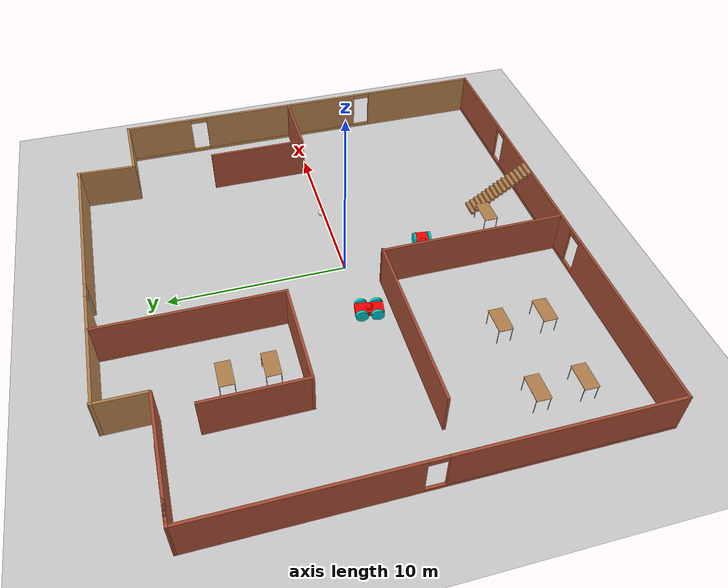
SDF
<sdf version="1.6">
 <world name="default">
  <plugin name="hello" filename="../build/libhello.so"/>
  <light name="sun" type="directional">
   <pose>0 0 10 0 -0 0</pose>
   <diffuse>0.8 0.8 0.8 1</diffuse>
   <specular>0.2 0.2 0.2 1</specular>
   <attenuation>
    <range>1000</range>
    <constant>0.9</constant>
    <linear>0.01</linear>
    <quadratic>0.001</quadratic>
   </attenuation>
   <direction>-0.5 0.1 -0.9</direction>
  </light>
  <model name="ground_plane">
   <static>1</static>
   <link name="link">
    <collision name="collision">
     <geometry><plane><normal>0 0 1</normal><size>100 100</size></plane></geometry>
     <surface>
      <contact><collide_bitmask>65535</collide_bitmask></contact>
      <friction><ode><mu>100</mu><mu2>50</mu2></ode></friction>
     </surface>
    </collision>
    <visual name="visual">
     <cast_shadows>0</cast_shadows>
     <geometry><plane><normal>0 0 1</normal><size>100 100</size></plane></geometry>
     <material>
      <script><uri>file://media/materials/scripts/gazebo.material</uri><name>Gazebo/Grey</name></script>
     </material>
    </visual>
   </link>
  </model>
  <gravity>0 0 -9.8</gravity>
  <magnetic_field>6e-06 2.3e-05 -4.2e-05</magnetic_field>
  <atmosphere type="adiabatic"/>
  <physics name="default_physics" default="0" type="ode">
   <max_step_size>0.001</max_step_size>
   <real_time_factor>1</real_time_factor>
   <real_time_update_rate>1000</real_time_update_rate>
  </physics>
  <scene><ambient>0.4 0.4 0.4 1</ambient><background>0.7 0.7 0.7 1</background><shadows>1</shadows></scene>
  <spherical_coordinates>
   <surface_model>EARTH_WGS84</surface_model>
   <latitude_deg>0</latitude_deg>
   <longitude_deg>0</longitude_deg>
   <elevation>0</elevation>
   <heading_deg>0</heading_deg>
  </spherical_coordinates>
  <model name="Office">
   <pose>-0.484509 0.848568 0 0 -0 0</pose>
   <link name="Stairs_0">
    <visual name="Stairs_0_Visual_0">
     <pose>3.3493 -9.60341 0.083333 0 -0 0</pose>
     <geometry><box><size>1 0.233333 0.166667</size></box></geometry>
     <material>
      <script><uri>file://media/materials/scripts/gazebo.material</uri><name>Gazebo/Wood</name></script>
      <ambient>1 1 1 1</ambient>
     </material>
     <meta><layer>0</layer></meta>
    </visual>
    <collision name="Stairs_0_Collision_0">
     <geometry><box><size>1 0.233333 0.166667</size></box></geometry>
     <pose>3.3493 -9.60341 0.083333 0 -0 0</pose>
    </collision>
    <visual name="Stairs_0_Visual_1">
     <pose>3.3493 -9.83674 0.25 0 -0 0</pose>
     <geometry><box><size>1 0.233333 0.166667</size></box></geometry>
     <material>
      <script><uri>file://media/materials/scripts/gazebo.material</uri><name>Gazebo/Wood</name></script>
      <ambient>1 1 1 1</ambient>
     </material>
     <meta><layer>0</layer></meta>
    </visual>
    <collision name="Stairs_0_Collision_1">
     <geometry><box><size>1 0.233333 0.166667</size></box></geometry>
     <pose>3.3493 -9.83674 0.25 0 -0 0</pose>
    </collision>
    <visual name="Stairs_0_Visual_2">
     <pose>3.3493 -10.0701 0.416667 0 -0 0</pose>
     <geometry><box><size>1 0.233333 0.166667</size></box></geometry>
     <material>
      <script><uri>file://media/materials/scripts/gazebo.material</uri><name>Gazebo/Wood</name></script>
      <ambient>1 1 1 1</ambient>
     </material>
     <meta><layer>0</layer></meta>
    </visual>
    <collision name="Stairs_0_Collision_2">
     <geometry><box><size>1 0.233333 0.166667</size></box></geometry>
     <pose>3.3493 -10.0701 0.416667 0 -0 0</pose>
    </collision>
    <visual name="Stairs_0_Visual_3">
     <pose>3.3493 -10.3034 0.583333 0 -0 0</pose>
     <geometry><box><size>1 0.233333 0.166667</size></box></geometry>
     <material>
      <script><uri>file://media/materials/scripts/gazebo.material</uri><name>Gazebo/Wood</name></script>
      <ambient>1 1 1 1</ambient>
     </material>
     <meta><layer>0</layer></meta>
    </visual>
    <collision name="Stairs_0_Collision_3">
     <geometry><box><size>1 0.233333 0.166667</size></box></geometry>
     <pose>3.3493 -10.3034 0.583333 0 -0 0</pose>
    </collision>
    <visual name="Stairs_0_Visual_4">
     <pose>3.3493 -10.5367 0.75 0 -0 0</pose>
     <geometry><box><size>1 0.233333 0.166667</size></box></geometry>
     <material>
      <script><uri>file://media/materials/scripts/gazebo.material</uri><name>Gazebo/Wood</name></script>
      <ambient>1 1 1 1</ambient>
     </material>
     <meta><layer>0</layer></meta>
    </visual>
    <collision name="Stairs_0_Collision_4">
     <geometry><box><size>1 0.233333 0.166667</size></box></geometry>
     <pose>3.3493 -10.5367 0.75 0 -0 0</pose>
    </collision>
    <visual name="Stairs_0_Visual_5">
     <pose>3.3493 -10.7701 0.916667 0 -0 0</pose>
     <geometry><box><size>1 0.233333 0.166667</size></box></geometry>
     <material>
      <script><uri>file://media/materials/scripts/gazebo.material</uri><name>Gazebo/Wood</name></script>
      <ambient>1 1 1 1</ambient>
     </material>
     <meta><layer>0</layer></meta>
    </visual>
    <collision name="Stairs_0_Collision_5">
     <geometry><box><size>1 0.233333 0.166667</size></box></geometry>
     <pose>3.3493 -10.7701 0.916667 0 -0 0</pose>
    </collision>
    <visual name="Stairs_0_Visual_6">
     <pose>3.3493 -11.0034 1.08333 0 -0 0</pose>
     <geometry><box><size>1 0.233333 0.166667</size></box></geometry>
     <material>
      <script><uri>file://media/materials/scripts/gazebo.material</uri><name>Gazebo/Wood</name></script>
      <ambient>1 1 1 1</ambient>
     </material>
     <meta><layer>0</layer></meta>
    </visual>
    <collision name="Stairs_0_Collision_6">
     <geometry><box><size>1 0.233333 0.166667</size></box></geometry>
     <pose>3.3493 -11.0034 1.08333 0 -0 0</pose>
    </collision>
    <visual name="Stairs_0_Visual_7">
     <pose>3.3493 -11.2367 1.25 0 -0 0</pose>
     <geometry><box><size>1 0.233333 0.166667</size></box></geometry>
     <material>
      <script><uri>file://media/materials/scripts/gazebo.material</uri><name>Gazebo/Wood</name></script>
      <ambient>1 1 1 1</ambient>
     </material>
     <meta><layer>0</layer></meta>
    </visual>
    <collision name="Stairs_0_Collision_7">
     <geometry><box><size>1 0.233333 0.166667</size></box></geometry>
     <pose>3.3493 -11.2367 1.25 0 -0 0</pose>
    </collision>
    <visual name="Stairs_0_Visual_8">
     <pose>3.3493 -11.4701 1.41667 0 -0 0</pose>
     <geometry><box><size>1 0.233333 0.166667</size></box></geometry>
     <material>
      <script><uri>file://media/materials/scripts/gazebo.material</uri><name>Gazebo/Wood</name></script>
      <ambient>1 1 1 1</ambient>
     </material>
     <meta><layer>0</layer></meta>
    </visual>
    <collision name="Stairs_0_Collision_8">
     <geometry><box><size>1 0.233333 0.166667</size></box></geometry>
     <pose>3.3493 -11.4701 1.41667 0 -0 0</pose>
    </collision>
    <visual name="Stairs_0_Visual_9">
     <pose>3.3493 -11.7034 1.58333 0 -0 0</pose>
     <geometry><box><size>1 0.233333 0.166667</size></box></geometry>
     <material>
      <script><uri>file://media/materials/scripts/gazebo.material</uri><name>Gazebo/Wood</name></script>
      <ambient>1 1 1 1</ambient>
     </material>
     <meta><layer>0</layer></meta>
    </visual>
    <collision name="Stairs_0_Collision_9">
     <geometry><box><size>1 0.233333 0.166667</size></box></geometry>
     <pose>3.3493 -11.7034 1.58333 0 -0 0</pose>
    </collision>
    <visual name="Stairs_0_Visual_10">
     <pose>3.3493 -11.9367 1.75 0 -0 0</pose>
     <geometry><box><size>1 0.233333 0.166667</size></box></geometry>
     <material>
      <script><uri>file://media/materials/scripts/gazebo.material</uri><name>Gazebo/Wood</name></script>
      <ambient>1 1 1 1</ambient>
     </material>
     <meta><layer>0</layer></meta>
    </visual>
    <collision name="Stairs_0_Collision_10">
     <geometry><box><size>1 0.233333 0.166667</size></box></geometry>
     <pose>3.3493 -11.9367 1.75 0 -0 0</pose>
    </collision>
    <visual name="Stairs_0_Visual_11">
     <pose>3.3493 -12.1701 1.91667 0 -0 0</pose>
     <geometry><box><size>1 0.233333 0.166667</size></box></geometry>
     <material>
      <script><uri>file://media/materials/scripts/gazebo.material</uri><name>Gazebo/Wood</name></script>
      <ambient>1 1 1 1</ambient>
     </material>
     <meta><layer>0</layer></meta>
    </visual>
    <collision name="Stairs_0_Collision_11">
     <geometry><box><size>1 0.233333 0.166667</size></box></geometry>
     <pose>3.3493 -12.1701 1.91667 0 -0 0</pose>
    </collision>
    <visual name="Stairs_0_Visual_12">
     <pose>3.3493 -12.4034 2.08333 0 -0 0</pose>
     <geometry><box><size>1 0.233333 0.166667</size></box></geometry>
     <material>
      <script><uri>file://media/materials/scripts/gazebo.material</uri><name>Gazebo/Wood</name></script>
      <ambient>1 1 1 1</ambient>
     </material>
     <meta><layer>0</layer></meta>
    </visual>
    <collision name="Stairs_0_Collision_12">
     <geometry><box><size>1 0.233333 0.166667</size></box></geometry>
     <pose>3.3493 -12.4034 2.08333 0 -0 0</pose>
    </collision>
    <visual name="Stairs_0_Visual_13">
     <pose>3.3493 -12.6367 2.25 0 -0 0</pose>
     <geometry><box><size>1 0.233333 0.166667</size></box></geometry>
     <material>
      <script><uri>file://media/materials/scripts/gazebo.material</uri><name>Gazebo/Wood</name></script>
      <ambient>1 1 1 1</ambient>
     </material>
     <meta><layer>0</layer></meta>
    </visual>
    <collision name="Stairs_0_Collision_13">
     <geometry><box><size>1 0.233333 0.166667</size></box></geometry>
     <pose>3.3493 -12.6367 2.25 0 -0 0</pose>
    </collision>
    <visual name="Stairs_0_Visual_14">
     <pose>3.3493 -12.8701 2.41667 0 -0 0</pose>
     <geometry><box><size>1 0.233333 0.166667</size></box></geometry>
     <material>
      <script><uri>file://media/materials/scripts/gazebo.material</uri><name>Gazebo/Wood</name></script>
      <ambient>1 1 1 1</ambient>
     </material>
     <meta><layer>0</layer></meta>
    </visual>
    <collision name="Stairs_0_Collision_14">
     <geometry><box><size>1 0.233333 0.166667</size></box></geometry>
     <pose>3.3493 -12.8701 2.41667 0 -0 0</pose>
    </collision>
   </link>
   <link name="Wall_0">
    <pose>-13.6665 -1.34581 0 0 -0 -1.5708</pose>
    <visual name="Wall_0_Visual_0">
     <pose>-6.25709 0 1.25 0 -0 0</pose>
     <geometry><box><size>10.9858 0.15 2.5</size></box></geometry>
     <material>
      <script><uri>file://media/materials/scripts/gazebo.material</uri><name>Gazebo/Bricks</name></script>
      <ambient>0.435294 0.796078 0.67451 1</ambient>
     </material>
     <meta><layer>0</layer></meta>
    </visual>
    <collision name="Wall_0_Collision_0">
     <geometry><box><size>10.9858 0.15 2.5</size></box></geometry>
     <pose>-6.25709 0 1.25 0 -0 0</pose>
    </collision>
    <visual name="Wall_0_Visual_1">
     <pose>5.49291 0 0.1 0 -0 0</pose>
     <geometry><box><size>12.5142 0.15 0.2</size></box></geometry>
     <material>
      <script><uri>file://media/materials/scripts/gazebo.material</uri><name>Gazebo/Bricks</name></script>
      <ambient>0.435294 0.796078 0.67451 1</ambient>
     </material>
     <meta><layer>0</layer></meta>
    </visual>
    <collision name="Wall_0_Collision_1">
     <geometry><box><size>12.5142 0.15 0.2</size></box></geometry>
     <pose>5.49291 0 0.1 0 -0 0</pose>
    </collision>
    <visual name="Wall_0_Visual_2">
     <pose>5.99291 0 1.35 0 -0 0</pose>
     <geometry><box><size>11.5142 0.15 2.3</size></box></geometry>
     <material>
      <script><uri>file://media/materials/scripts/gazebo.material</uri><name>Gazebo/Bricks</name></script>
      <ambient>0.435294 0.796078 0.67451 1</ambient>
     </material>
     <meta><layer>0</layer></meta>
    </visual>
    <collision name="Wall_0_Collision_2">
     <geometry><box><size>11.5142 0.15 2.3</size></box></geometry>
     <pose>5.99291 0 1.35 0 -0 0</pose>
    </collision>
    <visual name="Wall_0_Visual_3">
     <pose>-0.264183 0 2.35 0 -0 0</pose>
     <geometry><box><size>1 0.15 0.3</size></box></geometry>
     <material>
      <script><uri>file://media/materials/scripts/gazebo.material</uri><name>Gazebo/Bricks</name></script>
      <ambient>0.435294 0.796078 0.67451 1</ambient>
     </material>
     <meta><layer>0</layer></meta>
    </visual>
    <collision name="Wall_0_Collision_3">
     <geometry><box><size>1 0.15 0.3</size></box></geometry>
     <pose>-0.264183 0 2.35 0 -0 0</pose>
    </collision>
   </link>
   <link name="Wall_1">
    <pose>-0.000233 -13.0208 0 0 -0 0</pose>
    <visual name="Wall_1_Visual_0">
     <pose>-8.46246 0 1.25 0 -0 0</pose>
     <geometry><box><size>10.4647 0.15 2.5</size></box></geometry>
     <material>
      <script><uri>file://media/materials/scripts/gazebo.material</uri><name>Gazebo/Bricks</name></script>
      <ambient>0.435294 0.796078 0.67451 1</ambient>
     </material>
     <meta><layer>0</layer></meta>
    </visual>
    <collision name="Wall_1_Collision_0">
     <geometry><box><size>10.4647 0.15 2.5</size></box></geometry>
     <pose>-8.46246 0 1.25 0 -0 0</pose>
    </collision>
    <visual name="Wall_1_Visual_1">
     <pose>5.23233 0 0.1 0 -0 0</pose>
     <geometry><box><size>16.9249 0.15 0.2</size></box></geometry>
     <material>
      <script><uri>file://media/materials/scripts/gazebo.material</uri><name>Gazebo/Bricks</name></script>
      <ambient>0.435294 0.796078 0.67451 1</ambient>
     </material>
     <meta><layer>0</layer></meta>
    </visual>
    <collision name="Wall_1_Collision_1">
     <geometry><box><size>16.9249 0.15 0.2</size></box></geometry>
     <pose>5.23233 0 0.1 0 -0 0</pose>
    </collision>
    <visual name="Wall_1_Visual_2">
     <pose>2.28696 0 1.35 0 -0 0</pose>
     <geometry><box><size>9.0342 0.15 2.3</size></box></geometry>
     <material>
      <script><uri>file://media/materials/scripts/gazebo.material</uri><name>Gazebo/Bricks</name></script>
      <ambient>0.435294 0.796078 0.67451 1</ambient>
     </material>
     <meta><layer>0</layer></meta>
    </visual>
    <collision name="Wall_1_Collision_2">
     <geometry><box><size>9.0342 0.15 2.3</size></box></geometry>
     <pose>2.28696 0 1.35 0 -0 0</pose>
    </collision>
    <visual name="Wall_1_Visual_3">
     <pose>10.7494 0 1.35 0 -0 0</pose>
     <geometry><box><size>5.89072 0.15 2.3</size></box></geometry>
     <material>
      <script><uri>file://media/materials/scripts/gazebo.material</uri><name>Gazebo/Bricks</name></script>
      <ambient>0.435294 0.796078 0.67451 1</ambient>
     </material>
     <meta><layer>0</layer></meta>
    </visual>
    <collision name="Wall_1_Collision_3">
     <geometry><box><size>5.89072 0.15 2.3</size></box></geometry>
     <pose>10.7494 0 1.35 0 -0 0</pose>
    </collision>
    <visual name="Wall_1_Visual_4">
     <pose>-2.73014 0 2.35 0 -0 0</pose>
     <geometry><box><size>1 0.15 0.3</size></box></geometry>
     <material>
      <script><uri>file://media/materials/scripts/gazebo.material</uri><name>Gazebo/Bricks</name></script>
      <ambient>0.435294 0.796078 0.67451 1</ambient>
     </material>
     <meta><layer>0</layer></meta>
    </visual>
    <collision name="Wall_1_Collision_4">
     <geometry><box><size>1 0.15 0.3</size></box></geometry>
     <pose>-2.73014 0 2.35 0 -0 0</pose>
    </collision>
    <visual name="Wall_1_Visual_5">
     <pose>7.30406 0 2.35 0 -0 0</pose>
     <geometry><box><size>1 0.15 0.3</size></box></geometry>
     <material>
      <script><uri>file://media/materials/scripts/gazebo.material</uri><name>Gazebo/Bricks</name></script>
      <ambient>0.435294 0.796078 0.67451 1</ambient>
     </material>
     <meta><layer>0</layer></meta>
    </visual>
    <collision name="Wall_1_Collision_5">
     <geometry><box><size>1 0.15 0.3</size></box></geometry>
     <pose>7.30406 0 2.35 0 -0 0</pose>
    </collision>
   </link>
   <link name="Wall_10">
    <collision name="Wall_10_Collision">
     <geometry><box><size>10.4723 0.15 2.5</size></box></geometry>
     <pose>0 0 1.25 0 -0 0</pose>
    </collision>
    <visual name="Wall_10_Visual">
     <pose>0 0 1.25 0 -0 0</pose>
     <geometry><box><size>10.4723 0.15 2.5</size></box></geometry>
     <material>
      <script><uri>file://media/materials/scripts/gazebo.material</uri><name>Gazebo/Bricks</name></script>
      <ambient>1 1 1 1</ambient>
     </material>
     <meta><layer>0</layer></meta>
    </visual>
    <pose>-1.06028 -7.69746 0 0 -0 -1.56629</pose>
   </link>
   <link name="Wall_13">
    <collision name="Wall_13_Collision">
     <geometry><box><size>3.95311 0.15 2.5</size></box></geometry>
     <pose>0 0 1.25 0 -0 0</pose>
    </collision>
    <visual name="Wall_13_Visual">
     <pose>0 0 1.25 0 -0 0</pose>
     <geometry><box><size>3.95311 0.15 2.5</size></box></geometry>
     <material>
      <script><uri>file://media/materials/scripts/gazebo.material</uri><name>Gazebo/Bricks</name></script>
      <ambient>1 1 1 1</ambient>
     </material>
     <meta><layer>0</layer></meta>
    </visual>
    <pose>-11.765 10.3398 0 0 -0 -3.13603</pose>
   </link>
   <link name="Wall_14">
    <collision name="Wall_14_Collision">
     <geometry><box><size>6.75 0.15 2.5</size></box></geometry>
     <pose>0 0 1.25 0 -0 0</pose>
    </collision>
    <visual name="Wall_14_Visual">
     <pose>0 0 1.25 0 -0 0</pose>
     <geometry><box><size>6.75 0.15 2.5</size></box></geometry>
     <material>
      <script><uri>file://media/materials/scripts/gazebo.material</uri><name>Gazebo/Bricks</name></script>
      <ambient>1 1 1 1</ambient>
     </material>
     <meta><layer>0</layer></meta>
    </visual>
    <pose>-10.3665 10.3292 0 0 -0 0</pose>
   </link>
   <link name="Wall_16">
    <collision name="Wall_16_Collision">
     <geometry><box><size>5.75 0.15 2.5</size></box></geometry>
     <pose>0 0 1.25 0 -0 0</pose>
    </collision>
    <visual name="Wall_16_Visual">
     <pose>0 0 1.25 0 -0 0</pose>
     <geometry><box><size>5.75 0.15 2.5</size></box></geometry>
     <material>
      <script><uri>file://media/materials/scripts/gazebo.material</uri><name>Gazebo/Bricks</name></script>
      <ambient>1 1 1 1</ambient>
     </material>
     <meta><layer>0</layer></meta>
    </visual>
    <pose>9.53698 2.24663 0 0 -0 -1.5708</pose>
   </link>
   <link name="Wall_17">
    <collision name="Wall_17_Collision">
     <geometry><box><size>4 0.15 2.5</size></box></geometry>
     <pose>0 0 1.25 0 -0 0</pose>
    </collision>
    <visual name="Wall_17_Visual">
     <pose>0 0 1.25 0 -0 0</pose>
     <geometry><box><size>4 0.15 2.5</size></box></geometry>
     <material>
      <script><uri>file://media/materials/scripts/gazebo.material</uri><name>Gazebo/Bricks</name></script>
      <ambient>1 1 1 1</ambient>
     </material>
     <meta><layer>0</layer></meta>
    </visual>
    <pose>11.462 -0.55337 0 0 -0 0</pose>
   </link>
   <link name="Wall_18">
    <collision name="Wall_18_Collision">
     <geometry><box><size>0.25 0.15 2.5</size></box></geometry>
     <pose>0 0 1.25 0 -0 0</pose>
    </collision>
    <visual name="Wall_18_Visual">
     <pose>0 0 1.25 0 -0 0</pose>
     <geometry><box><size>0.25 0.15 2.5</size></box></geometry>
     <material>
      <script><uri>file://media/materials/scripts/gazebo.material</uri><name>Gazebo/Grey</name></script>
      <ambient>1 1 1 1</ambient>
     </material>
     <meta><layer>0</layer></meta>
    </visual>
    <pose>13.437 -0.55337 0 0 -0 0</pose>
   </link>
   <link name="Wall_2">
    <pose>13.6196 -1.59581 0 0 -0 1.5708</pose>
    <visual name="Wall_2_Visual_0">
     <pose>-7.98251 0 1.25 0 -0 0</pose>
     <geometry><box><size>7.03499 0.15 2.5</size></box></geometry>
     <material>
      <script><uri>file://media/materials/scripts/gazebo.material</uri><name>Gazebo/Wood</name></script>
      <ambient>1 1 1 1</ambient>
     </material>
     <meta><layer>0</layer></meta>
    </visual>
    <collision name="Wall_2_Collision_0">
     <geometry><box><size>7.03499 0.15 2.5</size></box></geometry>
     <pose>-7.98251 0 1.25 0 -0 0</pose>
    </collision>
    <visual name="Wall_2_Visual_1">
     <pose>3.51749 0 0.1 0 -0 0</pose>
     <geometry><box><size>15.965 0.15 0.2</size></box></geometry>
     <material>
      <script><uri>file://media/materials/scripts/gazebo.material</uri><name>Gazebo/Wood</name></script>
      <ambient>1 1 1 1</ambient>
     </material>
     <meta><layer>0</layer></meta>
    </visual>
    <collision name="Wall_2_Collision_1">
     <geometry><box><size>15.965 0.15 0.2</size></box></geometry>
     <pose>3.51749 0 0.1 0 -0 0</pose>
    </collision>
    <visual name="Wall_2_Visual_2">
     <pose>1.50191 0 1.35 0 -0 0</pose>
     <geometry><box><size>9.93385 0.15 2.3</size></box></geometry>
     <material>
      <script><uri>file://media/materials/scripts/gazebo.material</uri><name>Gazebo/Wood</name></script>
      <ambient>1 1 1 1</ambient>
     </material>
     <meta><layer>0</layer></meta>
    </visual>
    <collision name="Wall_2_Collision_2">
     <geometry><box><size>9.93385 0.15 2.3</size></box></geometry>
     <pose>1.50191 0 1.35 0 -0 0</pose>
    </collision>
    <visual name="Wall_2_Visual_3">
     <pose>9.48442 0 1.35 0 -0 0</pose>
     <geometry><box><size>4.03116 0.15 2.3</size></box></geometry>
     <material>
      <script><uri>file://media/materials/scripts/gazebo.material</uri><name>Gazebo/Wood</name></script>
      <ambient>1 1 1 1</ambient>
     </material>
     <meta><layer>0</layer></meta>
    </visual>
    <collision name="Wall_2_Collision_3">
     <geometry><box><size>4.03116 0.15 2.3</size></box></geometry>
     <pose>9.48442 0 1.35 0 -0 0</pose>
    </collision>
    <visual name="Wall_2_Visual_4">
     <pose>-3.96501 0 2.35 0 -0 0</pose>
     <geometry><box><size>1 0.15 0.3</size></box></geometry>
     <material>
      <script><uri>file://media/materials/scripts/gazebo.material</uri><name>Gazebo/Wood</name></script>
      <ambient>1 1 1 1</ambient>
     </material>
     <meta><layer>0</layer></meta>
    </visual>
    <collision name="Wall_2_Collision_4">
     <geometry><box><size>1 0.15 0.3</size></box></geometry>
     <pose>-3.96501 0 2.35 0 -0 0</pose>
    </collision>
    <visual name="Wall_2_Visual_5">
     <pose>6.96884 0 2.35 0 -0 0</pose>
     <geometry><box><size>1 0.15 0.3</size></box></geometry>
     <material>
      <script><uri>file://media/materials/scripts/gazebo.material</uri><name>Gazebo/Wood</name></script>
      <ambient>1 1 1 1</ambient>
     </material>
     <meta><layer>0</layer></meta>
    </visual>
    <collision name="Wall_2_Collision_5">
     <geometry><box><size>1 0.15 0.3</size></box></geometry>
     <pose>6.96884 0 2.35 0 -0 0</pose>
    </collision>
   </link>
   <link name="Wall_20">
    <collision name="Wall_20_Collision">
     <geometry><box><size>10 0.15 2.5</size></box></geometry>
     <pose>0 0 1.25 0 -0 0</pose>
    </collision>
    <visual name="Wall_20_Visual">
     <pose>0 0 1.25 0 -0 0</pose>
     <geometry><box><size>10 0.15 2.5</size></box></geometry>
     <material>
      <script><uri>file://media/materials/scripts/gazebo.material</uri><name>Gazebo/Bricks</name></script>
      <ambient>1 1 1 1</ambient>
     </material>
     <meta><layer>0</layer></meta>
    </visual>
    <pose>-2.60576 7.98417 0 0 -0 -1.5708</pose>
   </link>
   <link name="Wall_21">
    <collision name="Wall_21_Collision">
     <geometry><box><size>5.75 0.15 2.5</size></box></geometry>
     <pose>0 0 1.25 0 -0 0</pose>
    </collision>
    <visual name="Wall_21_Visual">
     <pose>0 0 1.25 0 -0 0</pose>
     <geometry><box><size>5.75 0.15 2.5</size></box></geometry>
     <material>
      <script><uri>file://media/materials/scripts/gazebo.material</uri><name>Gazebo/Bricks</name></script>
      <ambient>1 1 1 1</ambient>
     </material>
     <meta><layer>0</layer></meta>
    </visual>
    <pose>-5.40576 3.05917 0 0 -0 3.14159</pose>
   </link>
   <link name="Wall_22">
    <collision name="Wall_22_Collision">
     <geometry><box><size>5.5 0.15 2.5</size></box></geometry>
     <pose>0 0 1.25 0 -0 0</pose>
    </collision>
    <visual name="Wall_22_Visual">
     <pose>0 0 1.25 0 -0 0</pose>
     <geometry><box><size>5.5 0.15 2.5</size></box></geometry>
     <material>
      <script><uri>file://media/materials/scripts/gazebo.material</uri><name>Gazebo/Bricks</name></script>
      <ambient>1 1 1 1</ambient>
     </material>
     <meta><layer>0</layer></meta>
    </visual>
    <pose>-8.20576 5.73417 0 0 -0 1.5708</pose>
   </link>
   <link name="Wall_3">
    <collision name="Wall_3_Collision">
     <geometry><box><size>4.08454 0.15 2.5</size></box></geometry>
     <pose>0 0 1.25 0 -0 0</pose>
    </collision>
    <visual name="Wall_3_Visual">
     <pose>0 0 1.25 0 -0 0</pose>
     <geometry><box><size>4.08454 0.15 2.5</size></box></geometry>
     <material>
      <script><uri>file://media/materials/scripts/gazebo.material</uri><name>Gazebo/Wood</name></script>
      <ambient>1 1 1 1</ambient>
     </material>
     <meta><layer>0</layer></meta>
    </visual>
    <pose>11.6989 9.80593 0 0 -0 -3.12977</pose>
   </link>
   <link name="Wall_4">
    <collision name="Wall_4_Collision">
     <geometry><box><size>3.38799 0.15 2.5</size></box></geometry>
     <pose>0 0 1.25 0 -0 0</pose>
    </collision>
    <visual name="Wall_4_Visual">
     <pose>0 0 1.25 0 -0 0</pose>
     <geometry><box><size>3.38799 0.15 2.5</size></box></geometry>
     <material>
      <script><uri>file://media/materials/scripts/gazebo.material</uri><name>Gazebo/Wood</name></script>
      <ambient>1 1 1 1</ambient>
     </material>
     <meta><layer>0</layer></meta>
    </visual>
    <pose>9.75508 11.4002 0 0 -0 1.52768</pose>
   </link>
   <link name="Wall_5">
    <pose>1.39986 12.9711 0 0 -0 3.14159</pose>
    <visual name="Wall_5_Visual_0">
     <pose>-3.82584 0 1.25 0 -0 0</pose>
     <geometry><box><size>9.34832 0.15 2.5</size></box></geometry>
     <material>
      <script><uri>file://media/materials/scripts/gazebo.material</uri><name>Gazebo/Wood</name></script>
      <ambient>1 1 1 1</ambient>
     </material>
     <meta><layer>0</layer></meta>
    </visual>
    <collision name="Wall_5_Collision_0">
     <geometry><box><size>9.34832 0.15 2.5</size></box></geometry>
     <pose>-3.82584 0 1.25 0 -0 0</pose>
    </collision>
    <visual name="Wall_5_Visual_1">
     <pose>5.12416 0 1.25 0 -0 0</pose>
     <geometry><box><size>6.75168 0.15 2.5</size></box></geometry>
     <material>
      <script><uri>file://media/materials/scripts/gazebo.material</uri><name>Gazebo/Wood</name></script>
      <ambient>1 1 1 1</ambient>
     </material>
     <meta><layer>0</layer></meta>
    </visual>
    <collision name="Wall_5_Collision_1">
     <geometry><box><size>6.75168 0.15 2.5</size></box></geometry>
     <pose>5.12416 0 1.25 0 -0 0</pose>
    </collision>
    <visual name="Wall_5_Visual_2">
     <pose>1.29832 0 2.25 0 -0 0</pose>
     <geometry><box><size>0.9 0.15 0.5</size></box></geometry>
     <material>
      <script><uri>file://media/materials/scripts/gazebo.material</uri><name>Gazebo/Wood</name></script>
      <ambient>1 1 1 1</ambient>
     </material>
     <meta><layer>0</layer></meta>
    </visual>
    <collision name="Wall_5_Collision_2">
     <geometry><box><size>0.9 0.15 0.5</size></box></geometry>
     <pose>1.29832 0 2.25 0 -0 0</pose>
    </collision>
   </link>
   <link name="Wall_6">
    <collision name="Wall_6_Collision">
     <geometry><box><size>2.75 0.15 2.5</size></box></geometry>
     <pose>0 0 1.25 0 -0 0</pose>
    </collision>
    <visual name="Wall_6_Visual">
     <pose>0 0 1.25 0 -0 0</pose>
     <geometry><box><size>2.75 0.15 2.5</size></box></geometry>
     <material>
      <script><uri>file://media/materials/scripts/gazebo.material</uri><name>Gazebo/Wood</name></script>
      <ambient>1 1 1 1</ambient>
     </material>
     <meta><layer>0</layer></meta>
    </visual>
    <pose>-7.02514 11.7176 0 0 -0 -1.5708</pose>
   </link>
   <link name="Wall_9">
    <collision name="Wall_9_Collision">
     <geometry><box><size>10 0.15 2.5</size></box></geometry>
     <pose>0 0 1.25 0 -0 0</pose>
    </collision>
    <visual name="Wall_9_Visual">
     <pose>0 0 1.25 0 -0 0</pose>
     <geometry><box><size>10 0.15 2.5</size></box></geometry>
     <material>
      <script><uri>file://media/materials/scripts/gazebo.material</uri><name>Gazebo/Bricks</name></script>
      <ambient>1 1 1 1</ambient>
     </material>
     <meta><layer>0</layer></meta>
    </visual>
    <pose>-5.96202 -2.53677 0 0 -0 0</pose>
   </link>
   <static>1</static>
  </model>
  <model name="table_clone">
   <static>1</static>
   <link name="link">
    <collision name="surface">
     <pose>0 0 1 0 -0 0</pose>
     <geometry><box><size>1.5 0.8 0.03</size></box></geometry>
     <surface><friction><ode><mu>0.6</mu><mu2>0.6</mu2></ode></friction></surface>
    </collision>
    <visual name="visual1">
     <pose>0 0 1 0 -0 0</pose>
     <geometry><box><size>1.5 0.8 0.03</size></box></geometry>
     <material>
      <script><uri>file://media/materials/scripts/gazebo.material</uri><name>Gazebo/Wood</name></script>
     </material>
    </visual>
    <collision name="front_left_leg">
     <pose>0.68 0.38 0.5 0 -0 0</pose>
     <geometry><cylinder><radius>0.02</radius><length>1</length></cylinder></geometry>
    </collision>
    <visual name="front_left_leg">
     <pose>0.68 0.38 0.5 0 -0 0</pose>
     <geometry><cylinder><radius>0.02</radius><length>1</length></cylinder></geometry>
     <material>
      <script><uri>file://media/materials/scripts/gazebo.material</uri><name>Gazebo/Grey</name></script>
     </material>
    </visual>
    <collision name="front_right_leg">
     <pose>0.68 -0.38 0.5 0 -0 0</pose>
     <geometry><cylinder><radius>0.02</radius><length>1</length></cylinder></geometry>
    </collision>
    <visual name="front_right_leg">
     <pose>0.68 -0.38 0.5 0 -0 0</pose>
     <geometry><cylinder><radius>0.02</radius><length>1</length></cylinder></geometry>
     <material>
      <script><uri>file://media/materials/scripts/gazebo.material</uri><name>Gazebo/Grey</name></script>
     </material>
    </visual>
    <collision name="back_right_leg">
     <pose>-0.68 -0.38 0.5 0 -0 0</pose>
     <geometry><cylinder><radius>0.02</radius><length>1</length></cylinder></geometry>
    </collision>
    <visual name="back_right_leg">
     <pose>-0.68 -0.38 0.5 0 -0 0</pose>
     <geometry><cylinder><radius>0.02</radius><length>1</length></cylinder></geometry>
     <material>
      <script><uri>file://media/materials/scripts/gazebo.material</uri><name>Gazebo/Grey</name></script>
     </material>
    </visual>
    <collision name="back_left_leg">
     <pose>-0.68 0.38 0.5 0 -0 0</pose>
     <geometry><cylinder><radius>0.02</radius><length>1</length></cylinder></geometry>
    </collision>
    <visual name="back_left_leg">
     <pose>-0.68 0.38 0.5 0 -0 0</pose>
     <geometry><cylinder><radius>0.02</radius><length>1</length></cylinder></geometry>
     <material>
      <script><uri>file://media/materials/scripts/gazebo.material</uri><name>Gazebo/Grey</name></script>
     </material>
    </visual>
   </link>
   <pose>1.38828 -9.08582 0 0 -0 0</pose>
  </model>
  <model name="table_clone_1">
   <static>1</static>
   <link name="link">
    <collision name="surface">
     <pose>0 0 1 0 -0 0</pose>
     <geometry><box><size>1.5 0.8 0.03</size></box></geometry>
     <surface><friction><ode><mu>0.6</mu><mu2>0.6</mu2></ode></friction></surface>
    </collision>
    <visual name="visual1">
     <pose>0 0 1 0 -0 0</pose>
     <geometry><box><size>1.5 0.8 0.03</size></box></geometry>
     <material>
      <script><uri>file://media/materials/scripts/gazebo.material</uri><name>Gazebo/Wood</name></script>
     </material>
    </visual>
    <collision name="front_left_leg">
     <pose>0.68 0.38 0.5 0 -0 0</pose>
     <geometry><cylinder><radius>0.02</radius><length>1</length></cylinder></geometry>
    </collision>
    <visual name="front_left_leg">
     <pose>0.68 0.38 0.5 0 -0 0</pose>
     <geometry><cylinder><radius>0.02</radius><length>1</length></cylinder></geometry>
     <material>
      <script><uri>file://media/materials/scripts/gazebo.material</uri><name>Gazebo/Grey</name></script>
     </material>
    </visual>
    <collision name="front_right_leg">
     <pose>0.68 -0.38 0.5 0 -0 0</pose>
     <geometry><cylinder><radius>0.02</radius><length>1</length></cylinder></geometry>
    </collision>
    <visual name="front_right_leg">
     <pose>0.68 -0.38 0.5 0 -0 0</pose>
     <geometry><cylinder><radius>0.02</radius><length>1</length></cylinder></geometry>
     <material>
      <script><uri>file://media/materials/scripts/gazebo.material</uri><name>Gazebo/Grey</name></script>
     </material>
    </visual>
    <collision name="back_right_leg">
     <pose>-0.68 -0.38 0.5 0 -0 0</pose>
     <geometry><cylinder><radius>0.02</radius><length>1</length></cylinder></geometry>
    </collision>
    <visual name="back_right_leg">
     <pose>-0.68 -0.38 0.5 0 -0 0</pose>
     <geometry><cylinder><radius>0.02</radius><length>1</length></cylinder></geometry>
     <material>
      <script><uri>file://media/materials/scripts/gazebo.material</uri><name>Gazebo/Grey</name></script>
     </material>
    </visual>
    <collision name="back_left_leg">
     <pose>-0.68 0.38 0.5 0 -0 0</pose>
     <geometry><cylinder><radius>0.02</radius><length>1</length></cylinder></geometry>
    </collision>
    <visual name="back_left_leg">
     <pose>-0.68 0.38 0.5 0 -0 0</pose>
     <geometry><cylinder><radius>0.02</radius><length>1</length></cylinder></geometry>
     <material>
      <script><uri>file://media/materials/scripts/gazebo.material</uri><name>Gazebo/Grey</name></script>
     </material>
    </visual>
   </link>
   <pose>-6.61985 -6.50895 0 0 -0 0</pose>
  </model>
  <model name="table_clone_2">
   <static>1</static>
   <link name="link">
    <collision name="surface">
     <pose>0 0 1 0 -0 0</pose>
     <geometry><box><size>1.5 0.8 0.03</size></box></geometry>
     <surface><friction><ode><mu>0.6</mu><mu2>0.6</mu2></ode></friction></surface>
    </collision>
    <visual name="visual1">
     <pose>0 0 1 0 -0 0</pose>
     <geometry><box><size>1.5 0.8 0.03</size></box></geometry>
     <material>
      <script><uri>file://media/materials/scripts/gazebo.material</uri><name>Gazebo/Wood</name></script>
     </material>
    </visual>
    <collision name="front_left_leg">
     <pose>0.68 0.38 0.5 0 -0 0</pose>
     <geometry><cylinder><radius>0.02</radius><length>1</length></cylinder></geometry>
    </collision>
    <visual name="front_left_leg">
     <pose>0.68 0.38 0.5 0 -0 0</pose>
     <geometry><cylinder><radius>0.02</radius><length>1</length></cylinder></geometry>
     <material>
      <script><uri>file://media/materials/scripts/gazebo.material</uri><name>Gazebo/Grey</name></script>
     </material>
    </visual>
    <collision name="front_right_leg">
     <pose>0.68 -0.38 0.5 0 -0 0</pose>
     <geometry><cylinder><radius>0.02</radius><length>1</length></cylinder></geometry>
    </collision>
    <visual name="front_right_leg">
     <pose>0.68 -0.38 0.5 0 -0 0</pose>
     <geometry><cylinder><radius>0.02</radius><length>1</length></cylinder></geometry>
     <material>
      <script><uri>file://media/materials/scripts/gazebo.material</uri><name>Gazebo/Grey</name></script>
     </material>
    </visual>
    <collision name="back_right_leg">
     <pose>-0.68 -0.38 0.5 0 -0 0</pose>
     <geometry><cylinder><radius>0.02</radius><length>1</length></cylinder></geometry>
    </collision>
    <visual name="back_right_leg">
     <pose>-0.68 -0.38 0.5 0 -0 0</pose>
     <geometry><cylinder><radius>0.02</radius><length>1</length></cylinder></geometry>
     <material>
      <script><uri>file://media/materials/scripts/gazebo.material</uri><name>Gazebo/Grey</name></script>
     </material>
    </visual>
    <collision name="back_left_leg">
     <pose>-0.68 0.38 0.5 0 -0 0</pose>
     <geometry><cylinder><radius>0.02</radius><length>1</length></cylinder></geometry>
    </collision>
    <visual name="back_left_leg">
     <pose>-0.68 0.38 0.5 0 -0 0</pose>
     <geometry><cylinder><radius>0.02</radius><length>1</length></cylinder></geometry>
     <material>
      <script><uri>file://media/materials/scripts/gazebo.material</uri><name>Gazebo/Grey</name></script>
     </material>
    </visual>
   </link>
   <pose>-6.58542 -9 0 0 -0 0</pose>
  </model>
  <model name="table_clone_3">
   <static>1</static>
   <link name="link">
    <collision name="surface">
     <pose>0 0 1 0 -0 0</pose>
     <geometry><box><size>1.5 0.8 0.03</size></box></geometry>
     <surface><friction><ode><mu>0.6</mu><mu2>0.6</mu2></ode></friction></surface>
    </collision>
    <visual name="visual1">
     <pose>0 0 1 0 -0 0</pose>
     <geometry><box><size>1.5 0.8 0.03</size></box></geometry>
     <material>
      <script><uri>file://media/materials/scripts/gazebo.material</uri><name>Gazebo/Wood</name></script>
     </material>
    </visual>
    <collision name="front_left_leg">
     <pose>0.68 0.38 0.5 0 -0 0</pose>
     <geometry><cylinder><radius>0.02</radius><length>1</length></cylinder></geometry>
    </collision>
    <visual name="front_left_leg">
     <pose>0.68 0.38 0.5 0 -0 0</pose>
     <geometry><cylinder><radius>0.02</radius><length>1</length></cylinder></geometry>
     <material>
      <script><uri>file://media/materials/scripts/gazebo.material</uri><name>Gazebo/Grey</name></script>
     </material>
    </visual>
    <collision name="front_right_leg">
     <pose>0.68 -0.38 0.5 0 -0 0</pose>
     <geometry><cylinder><radius>0.02</radius><length>1</length></cylinder></geometry>
    </collision>
    <visual name="front_right_leg">
     <pose>0.68 -0.38 0.5 0 -0 0</pose>
     <geometry><cylinder><radius>0.02</radius><length>1</length></cylinder></geometry>
     <material>
      <script><uri>file://media/materials/scripts/gazebo.material</uri><name>Gazebo/Grey</name></script>
     </material>
    </visual>
    <collision name="back_right_leg">
     <pose>-0.68 -0.38 0.5 0 -0 0</pose>
     <geometry><cylinder><radius>0.02</radius><length>1</length></cylinder></geometry>
    </collision>
    <visual name="back_right_leg">
     <pose>-0.68 -0.38 0.5 0 -0 0</pose>
     <geometry><cylinder><radius>0.02</radius><length>1</length></cylinder></geometry>
     <material>
      <script><uri>file://media/materials/scripts/gazebo.material</uri><name>Gazebo/Grey</name></script>
     </material>
    </visual>
    <collision name="back_left_leg">
     <pose>-0.68 0.38 0.5 0 -0 0</pose>
     <geometry><cylinder><radius>0.02</radius><length>1</length></cylinder></geometry>
    </collision>
    <visual name="back_left_leg">
     <pose>-0.68 0.38 0.5 0 -0 0</pose>
     <geometry><cylinder><radius>0.02</radius><length>1</length></cylinder></geometry>
     <material>
      <script><uri>file://media/materials/scripts/gazebo.material</uri><name>Gazebo/Grey</name></script>
     </material>
    </visual>
   </link>
   <pose>-11 -9 0 0 -0 0</pose>
  </model>
  <model name="table_clone_4">
   <static>1</static>
   <link name="link">
    <collision name="surface">
     <pose>0 0 1 0 -0 0</pose>
     <geometry><box><size>1.5 0.8 0.03</size></box></geometry>
     <surface><friction><ode><mu>0.6</mu><mu2>0.6</mu2></ode></friction></surface>
    </collision>
    <visual name="visual1">
     <pose>0 0 1 0 -0 0</pose>
     <geometry><box><size>1.5 0.8 0.03</size></box></geometry>
     <material>
      <script><uri>file://media/materials/scripts/gazebo.material</uri><name>Gazebo/Wood</name></script>
     </material>
    </visual>
    <collision name="front_left_leg">
     <pose>0.68 0.38 0.5 0 -0 0</pose>
     <geometry><cylinder><radius>0.02</radius><length>1</length></cylinder></geometry>
    </collision>
    <visual name="front_left_leg">
     <pose>0.68 0.38 0.5 0 -0 0</pose>
     <geometry><cylinder><radius>0.02</radius><length>1</length></cylinder></geometry>
     <material>
      <script><uri>file://media/materials/scripts/gazebo.material</uri><name>Gazebo/Grey</name></script>
     </material>
    </visual>
    <collision name="front_right_leg">
     <pose>0.68 -0.38 0.5 0 -0 0</pose>
     <geometry><cylinder><radius>0.02</radius><length>1</length></cylinder></geometry>
    </collision>
    <visual name="front_right_leg">
     <pose>0.68 -0.38 0.5 0 -0 0</pose>
     <geometry><cylinder><radius>0.02</radius><length>1</length></cylinder></geometry>
     <material>
      <script><uri>file://media/materials/scripts/gazebo.material</uri><name>Gazebo/Grey</name></script>
     </material>
    </visual>
    <collision name="back_right_leg">
     <pose>-0.68 -0.38 0.5 0 -0 0</pose>
     <geometry><cylinder><radius>0.02</radius><length>1</length></cylinder></geometry>
    </collision>
    <visual name="back_right_leg">
     <pose>-0.68 -0.38 0.5 0 -0 0</pose>
     <geometry><cylinder><radius>0.02</radius><length>1</length></cylinder></geometry>
     <material>
      <script><uri>file://media/materials/scripts/gazebo.material</uri><name>Gazebo/Grey</name></script>
     </material>
    </visual>
    <collision name="back_left_leg">
     <pose>-0.68 0.38 0.5 0 -0 0</pose>
     <geometry><cylinder><radius>0.02</radius><length>1</length></cylinder></geometry>
    </collision>
    <visual name="back_left_leg">
     <pose>-0.68 0.38 0.5 0 -0 0</pose>
     <geometry><cylinder><radius>0.02</radius><length>1</length></cylinder></geometry>
     <material>
      <script><uri>file://media/materials/scripts/gazebo.material</uri><name>Gazebo/Grey</name></script>
     </material>
    </visual>
   </link>
   <pose>-11 -6.50895 0 0 -0 0</pose>
  </model>
  <model name="table_clone_clone_0">
   <static>1</static>
   <link name="link">
    <collision name="surface">
     <pose>0 0 1 0 -0 0</pose>
     <geometry><box><size>1.5 0.8 0.03</size></box></geometry>
     <surface><friction><ode><mu>0.6</mu><mu2>0.6</mu2></ode></friction></surface>
    </collision>
    <visual name="visual1">
     <pose>0 0 1 0 -0 0</pose>
     <geometry><box><size>1.5 0.8 0.03</size></box></geometry>
     <material>
      <script><uri>file://media/materials/scripts/gazebo.material</uri><name>Gazebo/Wood</name></script>
     </material>
    </visual>
    <collision name="front_left_leg">
     <pose>0.68 0.38 0.5 0 -0 0</pose>
     <geometry><cylinder><radius>0.02</radius><length>1</length></cylinder></geometry>
    </collision>
    <visual name="front_left_leg">
     <pose>0.68 0.38 0.5 0 -0 0</pose>
     <geometry><cylinder><radius>0.02</radius><length>1</length></cylinder></geometry>
     <material>
      <script><uri>file://media/materials/scripts/gazebo.material</uri><name>Gazebo/Grey</name></script>
     </material>
    </visual>
    <collision name="front_right_leg">
     <pose>0.68 -0.38 0.5 0 -0 0</pose>
     <geometry><cylinder><radius>0.02</radius><length>1</length></cylinder></geometry>
    </collision>
    <visual name="front_right_leg">
     <pose>0.68 -0.38 0.5 0 -0 0</pose>
     <geometry><cylinder><radius>0.02</radius><length>1</length></cylinder></geometry>
     <material>
      <script><uri>file://media/materials/scripts/gazebo.material</uri><name>Gazebo/Grey</name></script>
     </material>
    </visual>
    <collision name="back_right_leg">
     <pose>-0.68 -0.38 0.5 0 -0 0</pose>
     <geometry><cylinder><radius>0.02</radius><length>1</length></cylinder></geometry>
    </collision>
    <visual name="back_right_leg">
     <pose>-0.68 -0.38 0.5 0 -0 0</pose>
     <geometry><cylinder><radius>0.02</radius><length>1</length></cylinder></geometry>
     <material>
      <script><uri>file://media/materials/scripts/gazebo.material</uri><name>Gazebo/Grey</name></script>
     </material>
    </visual>
    <collision name="back_left_leg">
     <pose>-0.68 0.38 0.5 0 -0 0</pose>
     <geometry><cylinder><radius>0.02</radius><length>1</length></cylinder></geometry>
    </collision>
    <visual name="back_left_leg">
     <pose>-0.68 0.38 0.5 0 -0 0</pose>
     <geometry><cylinder><radius>0.02</radius><length>1</length></cylinder></geometry>
     <material>
      <script><uri>file://media/materials/scripts/gazebo.material</uri><name>Gazebo/Grey</name></script>
     </material>
    </visual>
   </link>
   <pose>-6.282 7.76109 0 0 -0 0</pose>
  </model>
  <model name="table_clone_clone_0_clone">
   <static>1</static>
   <link name="link">
    <collision name="surface">
     <pose>0 0 1 0 -0 0</pose>
     <geometry><box><size>1.5 0.8 0.03</size></box></geometry>
     <surface><friction><ode><mu>0.6</mu><mu2>0.6</mu2></ode></friction></surface>
    </collision>
    <visual name="visual1">
     <pose>0 0 1 0 -0 0</pose>
     <geometry><box><size>1.5 0.8 0.03</size></box></geometry>
     <material>
      <script><uri>file://media/materials/scripts/gazebo.material</uri><name>Gazebo/Wood</name></script>
     </material>
    </visual>
    <collision name="front_left_leg">
     <pose>0.68 0.38 0.5 0 -0 0</pose>
     <geometry><cylinder><radius>0.02</radius><length>1</length></cylinder></geometry>
    </collision>
    <visual name="front_left_leg">
     <pose>0.68 0.38 0.5 0 -0 0</pose>
     <geometry><cylinder><radius>0.02</radius><length>1</length></cylinder></geometry>
     <material>
      <script><uri>file://media/materials/scripts/gazebo.material</uri><name>Gazebo/Grey</name></script>
     </material>
    </visual>
    <collision name="front_right_leg">
     <pose>0.68 -0.38 0.5 0 -0 0</pose>
     <geometry><cylinder><radius>0.02</radius><length>1</length></cylinder></geometry>
    </collision>
    <visual name="front_right_leg">
     <pose>0.68 -0.38 0.5 0 -0 0</pose>
     <geometry><cylinder><radius>0.02</radius><length>1</length></cylinder></geometry>
     <material>
      <script><uri>file://media/materials/scripts/gazebo.material</uri><name>Gazebo/Grey</name></script>
     </material>
    </visual>
    <collision name="back_right_leg">
     <pose>-0.68 -0.38 0.5 0 -0 0</pose>
     <geometry><cylinder><radius>0.02</radius><length>1</length></cylinder></geometry>
    </collision>
    <visual name="back_right_leg">
     <pose>-0.68 -0.38 0.5 0 -0 0</pose>
     <geometry><cylinder><radius>0.02</radius><length>1</length></cylinder></geometry>
     <material>
      <script><uri>file://media/materials/scripts/gazebo.material</uri><name>Gazebo/Grey</name></script>
     </material>
    </visual>
    <collision name="back_left_leg">
     <pose>-0.68 0.38 0.5 0 -0 0</pose>
     <geometry><cylinder><radius>0.02</radius><length>1</length></cylinder></geometry>
    </collision>
    <visual name="back_left_leg">
     <pose>-0.68 0.38 0.5 0 -0 0</pose>
     <geometry><cylinder><radius>0.02</radius><length>1</length></cylinder></geometry>
     <material>
      <script><uri>file://media/materials/scripts/gazebo.material</uri><name>Gazebo/Grey</name></script>
     </material>
    </visual>
   </link>
   <pose>-6.282 5.4679 0 0 -0 0</pose>
  </model>
  <model name="beer">
   <link name="link">
    <pose>0 0 0.115 0 -0 0</pose>
    <inertial>
     <mass>0.39</mass>
     <inertia><ixx>0.00058</ixx><ixy>0</ixy><ixz>0</ixz><iyy>0.00058</iyy><iyz>0</iyz><izz>0.00019</izz></inertia>
    </inertial>
    <collision name="collision">
     <geometry><cylinder><radius>0.055</radius><length>0.23</length></cylinder></geometry>
    </collision>
    <visual name="visual">
     <geometry><cylinder><radius>0.055</radius><length>0.23</length></cylinder></geometry>
     <material>
      <script>
       <uri>model://beer/materials/scripts</uri>
       <uri>model://beer/materials/textures</uri>
       <name>Beer/Diffuse</name>
      </script>
     </material>
    </visual>
   </link>
   <pose>10.9311 2.18552 0.775001 7e-06 -1.5e-05 0.002639</pose>
  </model>
  <model name="beer_clone_0">
   <link name="link">
    <pose>0 0 0.115 0 -0 0</pose>
    <inertial>
     <mass>0.39</mass>
     <inertia><ixx>0.00058</ixx><ixy>0</ixy><ixz>0</ixz><iyy>0.00058</iyy><iyz>0</iyz><izz>0.00019</izz></inertia>
    </inertial>
    <collision name="collision">
     <geometry><cylinder><radius>0.055</radius><length>0.23</length></cylinder></geometry>
    </collision>
    <visual name="visual">
     <geometry><cylinder><radius>0.055</radius><length>0.23</length></cylinder></geometry>
     <material>
      <script>
       <uri>model://beer/materials/scripts</uri>
       <uri>model://beer/materials/textures</uri>
       <name>Beer/Diffuse</name>
      </script>
     </material>
    </visual>
   </link>
   <pose>11.0273 1.7807 0.775003 1.2e-05 5e-05 0.000279</pose>
  </model>
  <model name="table_clone_6">
   <static>1</static>
   <link name="link">
    <collision name="surface">
     <pose>0 0 1 0 -0 0</pose>
     <geometry><box><size>1.5 0.8 0.03</size></box></geometry>
     <surface><friction><ode><mu>0.6</mu><mu2>0.6</mu2></ode></friction></surface>
    </collision>
    <visual name="visual1">
     <pose>0 0 1 0 -0 0</pose>
     <geometry><box><size>1.5 0.8 0.03</size></box></geometry>
     <material>
      <script><uri>file://media/materials/scripts/gazebo.material</uri><name>Gazebo/Wood</name></script>
     </material>
    </visual>
    <collision name="front_left_leg">
     <pose>0.68 0.38 0.5 0 -0 0</pose>
     <geometry><cylinder><radius>0.02</radius><length>1</length></cylinder></geometry>
    </collision>
    <visual name="front_left_leg">
     <pose>0.68 0.38 0.5 0 -0 0</pose>
     <geometry><cylinder><radius>0.02</radius><length>1</length></cylinder></geometry>
     <material>
      <script><uri>file://media/materials/scripts/gazebo.material</uri><name>Gazebo/Grey</name></script>
     </material>
    </visual>
    <collision name="front_right_leg">
     <pose>0.68 -0.38 0.5 0 -0 0</pose>
     <geometry><cylinder><radius>0.02</radius><length>1</length></cylinder></geometry>
    </collision>
    <visual name="front_right_leg">
     <pose>0.68 -0.38 0.5 0 -0 0</pose>
     <geometry><cylinder><radius>0.02</radius><length>1</length></cylinder></geometry>
     <material>
      <script><uri>file://media/materials/scripts/gazebo.material</uri><name>Gazebo/Grey</name></script>
     </material>
    </visual>
    <collision name="back_right_leg">
     <pose>-0.68 -0.38 0.5 0 -0 0</pose>
     <geometry><cylinder><radius>0.02</radius><length>1</length></cylinder></geometry>
    </collision>
    <visual name="back_right_leg">
     <pose>-0.68 -0.38 0.5 0 -0 0</pose>
     <geometry><cylinder><radius>0.02</radius><length>1</length></cylinder></geometry>
     <material>
      <script><uri>file://media/materials/scripts/gazebo.material</uri><name>Gazebo/Grey</name></script>
     </material>
    </visual>
    <collision name="back_left_leg">
     <pose>-0.68 0.38 0.5 0 -0 0</pose>
     <geometry><cylinder><radius>0.02</radius><length>1</length></cylinder></geometry>
    </collision>
    <visual name="back_left_leg">
     <pose>-0.68 0.38 0.5 0 -0 0</pose>
     <geometry><cylinder><radius>0.02</radius><length>1</length></cylinder></geometry>
     <material>
      <script><uri>file://media/materials/scripts/gazebo.material</uri><name>Gazebo/Grey</name></script>
     </material>
    </visual>
   </link>
   <pose>-0.574197 -12.5811 0 0 -0 0</pose>
  </model>
  <model name="4wheeler">
   <link name="link_0">
    <inertial>
     <mass>1.35085</mass>
     <inertia>
      <ixx>0.277852</ixx>
      <ixy>0</ixy>
      <ixz>0</ixz>
      <iyy>0.0669791</iyy>
      <iyz>0</iyz>
      <izz>0.321192</izz>
     </inertia>
    </inertial>
    <pose>0.011609 -0.00021 0.4 0 -0 0</pose>
    <visual name="visual">
     <geometry><box><size>0.7 1.53729 0.324029</size></box></geometry>
     <material>
      <lighting>1</lighting>
      <script><uri>file://media/materials/scripts/gazebo.material</uri><name>Gazebo/Grey</name></script>
      <shader type="pixel"><normal_map>__default__</normal_map></shader>
      <ambient>1 0 0 1</ambient>
      <diffuse>0.7 0.7 0.7 1</diffuse>
      <specular>0.01 0.01 0.01 1</specular>
      <emissive>0 0 0 1</emissive>
     </material>
    </visual>
    <collision name="collision">
     <geometry><box><size>0.7 1.53729 0.324029</size></box></geometry>
     <surface>
      <friction>
       <ode><mu>1</mu><mu2>1</mu2><fdir1>0 0 0</fdir1><slip1>0</slip1><slip2>0</slip2></ode>
       <torsional>
        <coefficient>1</coefficient>
        <patch_radius>0</patch_radius>
        <surface_radius>0</surface_radius>
        <use_patch_radius>1</use_patch_radius>
        <ode><slip>0</slip></ode>
       </torsional>
      </friction>
      <bounce><restitution_coefficient>0</restitution_coefficient><threshold>1e+06</threshold></bounce>
      <contact>
       <collide_without_contact>0</collide_without_contact>
       <collide_without_contact_bitmask>1</collide_without_contact_bitmask>
       <collide_bitmask>1</collide_bitmask>
       <ode>
        <soft_cfm>0</soft_cfm>
        <soft_erp>0.2</soft_erp>
        <kp>1e+13</kp>
        <kd>1</kd>
        <max_vel>0.01</max_vel>
        <min_depth>0</min_depth>
       </ode>
       <bullet>
        <split_impulse>1</split_impulse>
        <split_impulse_penetration_threshold>-0.01</split_impulse_penetration_threshold>
        <soft_cfm>0</soft_cfm>
        <soft_erp>0.2</soft_erp>
        <kp>1e+13</kp>
        <kd>1</kd>
       </bullet>
      </contact>
     </surface>
    </collision>
   </link>
   <link name="link_1_clone">
    <inertial>
     <mass>1</mass>
     <inertia><ixx>0.145833</ixx><ixy>0</ixy><ixz>0</ixz><iyy>0.145833</iyy><iyz>0</iyz><izz>0.125</izz></inertia>
    </inertial>
    <pose>0.44037 0.416058 0.4 1.5707 0 1.5707</pose>
    <visual name="visual">
     <geometry><cylinder><radius>0.35</radius><length>0.15</length></cylinder></geometry>
     <material>
      <lighting>1</lighting>
      <script><uri>file://media/materials/scripts/gazebo.material</uri><name>Gazebo/Grey</name></script>
      <shader type="pixel"><normal_map>__default__</normal_map></shader>
      <ambient>0 0.8 0.8 1</ambient>
      <diffuse>0.7 0.7 0.7 1</diffuse>
      <specular>0.01 0.01 0.01 1</specular>
      <emissive>0 0 0 1</emissive>
     </material>
    </visual>
    <collision name="collision">
     <geometry><cylinder><radius>0.35</radius><length>0.15</length></cylinder></geometry>
     <surface>
      <friction>
       <ode><mu>1</mu><mu2>1</mu2><fdir1>0 0 0</fdir1><slip1>0</slip1><slip2>0</slip2></ode>
       <torsional>
        <coefficient>1</coefficient>
        <patch_radius>0</patch_radius>
        <surface_radius>0</surface_radius>
        <use_patch_radius>1</use_patch_radius>
        <ode><slip>0</slip></ode>
       </torsional>
      </friction>
      <bounce><restitution_coefficient>0</restitution_coefficient><threshold>1e+06</threshold></bounce>
      <contact>
       <collide_without_contact>0</collide_without_contact>
       <collide_without_contact_bitmask>1</collide_without_contact_bitmask>
       <collide_bitmask>1</collide_bitmask>
       <ode>
        <soft_cfm>0</soft_cfm>
        <soft_erp>0.2</soft_erp>
        <kp>1e+13</kp>
        <kd>1</kd>
        <max_vel>0.01</max_vel>
        <min_depth>0</min_depth>
       </ode>
       <bullet>
        <split_impulse>1</split_impulse>
        <split_impulse_penetration_threshold>-0.01</split_impulse_penetration_threshold>
        <soft_cfm>0</soft_cfm>
        <soft_erp>0.2</soft_erp>
        <kp>1e+13</kp>
        <kd>1</kd>
       </bullet>
      </contact>
     </surface>
    </collision>
   </link>
   <link name="link_1_clone_clone">
    <inertial>
     <mass>1</mass>
     <inertia><ixx>0.145833</ixx><ixy>0</ixy><ixz>0</ixz><iyy>0.145833</iyy><iyz>0</iyz><izz>0.125</izz></inertia>
    </inertial>
    <pose>0.431165 -0.424592 0.4 1.5707 0 1.5707</pose>
    <visual name="visual">
     <geometry><cylinder><radius>0.35</radius><length>0.15</length></cylinder></geometry>
     <material>
      <lighting>1</lighting>
      <script><uri>file://media/materials/scripts/gazebo.material</uri><name>Gazebo/Grey</name></script>
      <shader type="pixel"><normal_map>__default__</normal_map></shader>
      <ambient>0 0.8 0.8 1</ambient>
      <diffuse>0.7 0.7 0.7 1</diffuse>
      <specular>0.01 0.01 0.01 1</specular>
      <emissive>0 0 0 1</emissive>
     </material>
    </visual>
    <collision name="collision">
     <geometry><cylinder><radius>0.35</radius><length>0.15</length></cylinder></geometry>
     <surface>
      <friction>
       <ode><mu>1</mu><mu2>1</mu2><fdir1>0 0 0</fdir1><slip1>0</slip1><slip2>0</slip2></ode>
       <torsional>
        <coefficient>1</coefficient>
        <patch_radius>0</patch_radius>
        <surface_radius>0</surface_radius>
        <use_patch_radius>1</use_patch_radius>
        <ode><slip>0</slip></ode>
       </torsional>
      </friction>
      <bounce><restitution_coefficient>0</restitution_coefficient><threshold>1e+06</threshold></bounce>
      <contact>
       <collide_without_contact>0</collide_without_contact>
       <collide_without_contact_bitmask>1</collide_without_contact_bitmask>
       <collide_bitmask>1</collide_bitmask>
       <ode>
        <soft_cfm>0</soft_cfm>
        <soft_erp>0.2</soft_erp>
        <kp>1e+13</kp>
        <kd>1</kd>
        <max_vel>0.01</max_vel>
        <min_depth>0</min_depth>
       </ode>
       <bullet>
        <split_impulse>1</split_impulse>
        <split_impulse_penetration_threshold>-0.01</split_impulse_penetration_threshold>
        <soft_cfm>0</soft_cfm>
        <soft_erp>0.2</soft_erp>
        <kp>1e+13</kp>
        <kd>1</kd>
       </bullet>
      </contact>
     </surface>
    </collision>
   </link>
   <link name="link_1_clone_clone_0">
    <inertial>
     <mass>1</mass>
     <inertia><ixx>0.145833</ixx><ixy>0</ixy><ixz>0</ixz><iyy>0.145833</iyy><iyz>0</iyz><izz>0.125</izz></inertia>
    </inertial>
    <pose>-0.421453 0.42237 0.4 1.5707 0 1.5707</pose>
    <visual name="visual">
     <geometry><cylinder><radius>0.35</radius><length>0.15</length></cylinder></geometry>
     <material>
      <lighting>1</lighting>
      <script><uri>file://media/materials/scripts/gazebo.material</uri><name>Gazebo/Grey</name></script>
      <shader type="pixel"><normal_map>__default__</normal_map></shader>
      <ambient>0 0.8 0.8 1</ambient>
      <diffuse>0.7 0.7 0.7 1</diffuse>
      <specular>0.01 0.01 0.01 1</specular>
      <emissive>0 0 0 1</emissive>
     </material>
    </visual>
    <collision name="collision">
     <geometry><cylinder><radius>0.35</radius><length>0.15</length></cylinder></geometry>
     <surface>
      <friction>
       <ode><mu>1</mu><mu2>1</mu2><fdir1>0 0 0</fdir1><slip1>0</slip1><slip2>0</slip2></ode>
       <torsional>
        <coefficient>1</coefficient>
        <patch_radius>0</patch_radius>
        <surface_radius>0</surface_radius>
        <use_patch_radius>1</use_patch_radius>
        <ode><slip>0</slip></ode>
       </torsional>
      </friction>
      <bounce><restitution_coefficient>0</restitution_coefficient><threshold>1e+06</threshold></bounce>
      <contact>
       <collide_without_contact>0</collide_without_contact>
       <collide_without_contact_bitmask>1</collide_without_contact_bitmask>
       <collide_bitmask>1</collide_bitmask>
       <ode>
        <soft_cfm>0</soft_cfm>
        <soft_erp>0.2</soft_erp>
        <kp>1e+13</kp>
        <kd>1</kd>
        <max_vel>0.01</max_vel>
        <min_depth>0</min_depth>
       </ode>
       <bullet>
        <split_impulse>1</split_impulse>
        <split_impulse_penetration_threshold>-0.01</split_impulse_penetration_threshold>
        <soft_cfm>0</soft_cfm>
        <soft_erp>0.2</soft_erp>
        <kp>1e+13</kp>
        <kd>1</kd>
       </bullet>
      </contact>
     </surface>
    </collision>
   </link>
   <link name="link_1_clone_clone_clone">
    <inertial>
     <mass>1</mass>
     <inertia><ixx>0.145833</ixx><ixy>0</ixy><ixz>0</ixz><iyy>0.145833</iyy><iyz>0</iyz><izz>0.125</izz></inertia>
    </inertial>
    <pose>-0.415948 -0.421035 0.4 1.5707 0 1.5707</pose>
    <visual name="visual">
     <geometry><cylinder><radius>0.35</radius><length>0.15</length></cylinder></geometry>
     <material>
      <lighting>1</lighting>
      <script><uri>file://media/materials/scripts/gazebo.material</uri><name>Gazebo/Grey</name></script>
      <shader type="pixel"><normal_map>__default__</normal_map></shader>
      <ambient>0 0.8 0.8 1</ambient>
      <diffuse>0.7 0.7 0.7 1</diffuse>
      <specular>0.01 0.01 0.01 1</specular>
      <emissive>0 0 0 1</emissive>
     </material>
    </visual>
    <collision name="collision">
     <geometry><cylinder><radius>0.35</radius><length>0.15</length></cylinder></geometry>
     <surface>
      <friction>
       <ode><mu>1</mu><mu2>1</mu2><fdir1>0 0 0</fdir1><slip1>0</slip1><slip2>0</slip2></ode>
       <torsional>
        <coefficient>1</coefficient>
        <patch_radius>0</patch_radius>
        <surface_radius>0</surface_radius>
        <use_patch_radius>1</use_patch_radius>
        <ode><slip>0</slip></ode>
       </torsional>
      </friction>
      <bounce><restitution_coefficient>0</restitution_coefficient><threshold>1e+06</threshold></bounce>
      <contact>
       <collide_without_contact>0</collide_without_contact>
       <collide_without_contact_bitmask>1</collide_without_contact_bitmask>
       <collide_bitmask>1</collide_bitmask>
       <ode>
        <soft_cfm>0</soft_cfm>
        <soft_erp>0.2</soft_erp>
        <kp>1e+13</kp>
        <kd>1</kd>
        <max_vel>0.01</max_vel>
        <min_depth>0</min_depth>
       </ode>
       <bullet>
        <split_impulse>1</split_impulse>
        <split_impulse_penetration_threshold>-0.01</split_impulse_penetration_threshold>
        <soft_cfm>0</soft_cfm>
        <soft_erp>0.2</soft_erp>
        <kp>1e+13</kp>
        <kd>1</kd>
       </bullet>
      </contact>
     </surface>
    </collision>
   </link>
   <link name="link_5">
    <inertial>
     <mass>1</mass>
     <inertia><ixx>0.1</ixx><ixy>0</ixy><ixz>0</ixz><iyy>0.1</iyy><iyz>0</iyz><izz>0.1</izz></inertia>
    </inertial>
    <pose>-0.001788 -0.009431 0.6 0 -0 0</pose>
    <visual name="visual">
     <geometry><sphere><radius>0.2</radius></sphere></geometry>
     <material>
      <lighting>1</lighting>
      <script><uri>file://media/materials/scripts/gazebo.material</uri><name>Gazebo/Grey</name></script>
      <shader type="pixel"><normal_map>__default__</normal_map></shader>
      <ambient>1 0 0 1</ambient>
      <diffuse>0.7 0.7 0.7 1</diffuse>
      <specular>0.01 0.01 0.01 1</specular>
      <emissive>0 0 0 1</emissive>
     </material>
    </visual>
    <collision name="collision">
     <geometry><sphere><radius>0.2</radius></sphere></geometry>
     <surface>
      <friction>
       <ode><mu>1</mu><mu2>1</mu2><fdir1>0 0 0</fdir1><slip1>0</slip1><slip2>0</slip2></ode>
       <torsional>
        <coefficient>1</coefficient>
        <patch_radius>0</patch_radius>
        <surface_radius>0</surface_radius>
        <use_patch_radius>1</use_patch_radius>
        <ode><slip>0</slip></ode>
       </torsional>
      </friction>
      <bounce><restitution_coefficient>0</restitution_coefficient><threshold>1e+06</threshold></bounce>
      <contact>
       <collide_without_contact>0</collide_without_contact>
       <collide_without_contact_bitmask>1</collide_without_contact_bitmask>
       <collide_bitmask>1</collide_bitmask>
       <ode>
        <soft_cfm>0</soft_cfm>
        <soft_erp>0.2</soft_erp>
        <kp>1e+13</kp>
        <kd>1</kd>
        <max_vel>0.01</max_vel>
        <min_depth>0</min_depth>
       </ode>
       <bullet>
        <split_impulse>1</split_impulse>
        <split_impulse_penetration_threshold>-0.01</split_impulse_penetration_threshold>
        <soft_cfm>0</soft_cfm>
        <soft_erp>0.2</soft_erp>
        <kp>1e+13</kp>
        <kd>1</kd>
       </bullet>
      </contact>
     </surface>
    </collision>
   </link>
   <joint name="link_0_JOINT_0" type="revolute">
    <parent>link_0</parent>
    <child>link_1_clone</child>
    <axis>
     <xyz>0 0 1</xyz>
     <use_parent_model_frame>0</use_parent_model_frame>
     <limit>
      <lower>-1.79769e+308</lower>
      <upper>1.79769e+308</upper>
      <effort>-1</effort>
      <velocity>-1</velocity>
     </limit>
     <dynamics>
      <spring_reference>0</spring_reference>
      <spring_stiffness>0</spring_stiffness>
      <damping>0</damping>
      <friction>0</friction>
     </dynamics>
    </axis>
    <physics>
     <ode><limit><cfm>0</cfm><erp>0.2</erp></limit><suspension><cfm>0</cfm><erp>0.2</erp></suspension></ode>
    </physics>
   </joint>
   <joint name="link_0_JOINT_1" type="revolute">
    <parent>link_0</parent>
    <child>link_1_clone_clone</child>
    <axis>
     <xyz>0 0 1</xyz>
     <use_parent_model_frame>0</use_parent_model_frame>
     <limit>
      <lower>-1.79769e+308</lower>
      <upper>1.79769e+308</upper>
      <effort>-1</effort>
      <velocity>-1</velocity>
     </limit>
     <dynamics>
      <spring_reference>0</spring_reference>
      <spring_stiffness>0</spring_stiffness>
      <damping>0</damping>
      <friction>0</friction>
     </dynamics>
    </axis>
    <physics>
     <ode><limit><cfm>0</cfm><erp>0.2</erp></limit><suspension><cfm>0</cfm><erp>0.2</erp></suspension></ode>
    </physics>
   </joint>
   <joint name="link_0_JOINT_2" type="revolute">
    <parent>link_0</parent>
    <child>link_1_clone_clone_clone</child>
    <axis>
     <xyz>0 0 1</xyz>
     <use_parent_model_frame>0</use_parent_model_frame>
     <limit>
      <lower>-1.79769e+308</lower>
      <upper>1.79769e+308</upper>
      <effort>-1</effort>
      <velocity>-1</velocity>
     </limit>
     <dynamics>
      <spring_reference>0</spring_reference>
      <spring_stiffness>0</spring_stiffness>
      <damping>0</damping>
      <friction>0</friction>
     </dynamics>
    </axis>
    <physics>
     <ode><limit><cfm>0</cfm><erp>0.2</erp></limit><suspension><cfm>0</cfm><erp>0.2</erp></suspension></ode>
    </physics>
   </joint>
   <joint name="link_0_JOINT_3" type="revolute">
    <parent>link_0</parent>
    <child>link_1_clone_clone_0</child>
    <axis>
     <xyz>1 0 0</xyz>
     <use_parent_model_frame>0</use_parent_model_frame>
     <limit>
      <lower>-1.79769e+308</lower>
      <upper>1.79769e+308</upper>
      <effort>-1</effort>
      <velocity>-1</velocity>
     </limit>
     <dynamics>
      <spring_reference>0</spring_reference>
      <spring_stiffness>0</spring_stiffness>
      <damping>0</damping>
      <friction>0</friction>
     </dynamics>
    </axis>
    <physics>
     <ode><limit><cfm>0</cfm><erp>0.2</erp></limit><suspension><cfm>0</cfm><erp>0.2</erp></suspension></ode>
    </physics>
   </joint>
   <joint name="link_0_JOINT_4" type="fixed">
    <parent>link_0</parent>
    <child>link_5</child>
    <physics>
     <ode><limit><cfm>0</cfm><erp>0.2</erp></limit><suspension><cfm>0</cfm><erp>0.2</erp></suspension></ode>
    </physics>
   </joint>
   <static>0</static>
   <pose>0.437655 -4.80688 -0.049993 2e-06 -4e-06 -1.69809</pose>
  </model>
  <model name="4wheeler_0">
   <link name="link_0">
    <inertial>
     <mass>1.35085</mass>
     <inertia>
      <ixx>0.277852</ixx>
      <ixy>0</ixy>
      <ixz>0</ixz>
      <iyy>0.0669791</iyy>
      <iyz>0</iyz>
      <izz>0.321192</izz>
     </inertia>
    </inertial>
    <pose>0.011609 -0.00021 0.4 0 -0 0</pose>
    <visual name="visual">
     <geometry><box><size>0.7 1.53729 0.324029</size></box></geometry>
     <material>
      <lighting>1</lighting>
      <script><uri>file://media/materials/scripts/gazebo.material</uri><name>Gazebo/Grey</name></script>
      <shader type="pixel"><normal_map>__default__</normal_map></shader>
      <ambient>1 0 0 1</ambient>
      <diffuse>0.7 0.7 0.7 1</diffuse>
      <specular>0.01 0.01 0.01 1</specular>
      <emissive>0 0 0 1</emissive>
     </material>
    </visual>
    <collision name="collision">
     <geometry><box><size>0.7 1.53729 0.324029</size></box></geometry>
     <surface>
      <friction>
       <ode><mu>1</mu><mu2>1</mu2><fdir1>0 0 0</fdir1><slip1>0</slip1><slip2>0</slip2></ode>
       <torsional>
        <coefficient>1</coefficient>
        <patch_radius>0</patch_radius>
        <surface_radius>0</surface_radius>
        <use_patch_radius>1</use_patch_radius>
        <ode><slip>0</slip></ode>
       </torsional>
      </friction>
      <bounce><restitution_coefficient>0</restitution_coefficient><threshold>1e+06</threshold></bounce>
      <contact>
       <collide_without_contact>0</collide_without_contact>
       <collide_without_contact_bitmask>1</collide_without_contact_bitmask>
       <collide_bitmask>1</collide_bitmask>
       <ode>
        <soft_cfm>0</soft_cfm>
        <soft_erp>0.2</soft_erp>
        <kp>1e+13</kp>
        <kd>1</kd>
        <max_vel>0.01</max_vel>
        <min_depth>0</min_depth>
       </ode>
       <bullet>
        <split_impulse>1</split_impulse>
        <split_impulse_penetration_threshold>-0.01</split_impulse_penetration_threshold>
        <soft_cfm>0</soft_cfm>
        <soft_erp>0.2</soft_erp>
        <kp>1e+13</kp>
        <kd>1</kd>
       </bullet>
      </contact>
     </surface>
    </collision>
   </link>
   <link name="link_1_clone">
    <inertial>
     <mass>1</mass>
     <inertia><ixx>0.145833</ixx><ixy>0</ixy><ixz>0</ixz><iyy>0.145833</iyy><iyz>0</iyz><izz>0.125</izz></inertia>
    </inertial>
    <pose>0.44037 0.416058 0.4 1.5707 0 1.5707</pose>
    <visual name="visual">
     <geometry><cylinder><radius>0.35</radius><length>0.15</length></cylinder></geometry>
     <material>
      <lighting>1</lighting>
      <script><uri>file://media/materials/scripts/gazebo.material</uri><name>Gazebo/Grey</name></script>
      <shader type="pixel"><normal_map>__default__</normal_map></shader>
      <ambient>0 0.8 0.8 1</ambient>
      <diffuse>0.7 0.7 0.7 1</diffuse>
      <specular>0.01 0.01 0.01 1</specular>
      <emissive>0 0 0 1</emissive>
     </material>
    </visual>
    <collision name="collision">
     <geometry><cylinder><radius>0.35</radius><length>0.15</length></cylinder></geometry>
     <surface>
      <friction>
       <ode><mu>1</mu><mu2>1</mu2><fdir1>0 0 0</fdir1><slip1>0</slip1><slip2>0</slip2></ode>
       <torsional>
        <coefficient>1</coefficient>
        <patch_radius>0</patch_radius>
        <surface_radius>0</surface_radius>
        <use_patch_radius>1</use_patch_radius>
        <ode><slip>0</slip></ode>
       </torsional>
      </friction>
      <bounce><restitution_coefficient>0</restitution_coefficient><threshold>1e+06</threshold></bounce>
      <contact>
       <collide_without_contact>0</collide_without_contact>
       <collide_without_contact_bitmask>1</collide_without_contact_bitmask>
       <collide_bitmask>1</collide_bitmask>
       <ode>
        <soft_cfm>0</soft_cfm>
        <soft_erp>0.2</soft_erp>
        <kp>1e+13</kp>
        <kd>1</kd>
        <max_vel>0.01</max_vel>
        <min_depth>0</min_depth>
       </ode>
       <bullet>
        <split_impulse>1</split_impulse>
        <split_impulse_penetration_threshold>-0.01</split_impulse_penetration_threshold>
        <soft_cfm>0</soft_cfm>
        <soft_erp>0.2</soft_erp>
        <kp>1e+13</kp>
        <kd>1</kd>
       </bullet>
      </contact>
     </surface>
    </collision>
   </link>
   <link name="link_1_clone_clone">
    <inertial>
     <mass>1</mass>
     <inertia><ixx>0.145833</ixx><ixy>0</ixy><ixz>0</ixz><iyy>0.145833</iyy><iyz>0</iyz><izz>0.125</izz></inertia>
    </inertial>
    <pose>0.431165 -0.424592 0.4 1.5707 0 1.5707</pose>
    <visual name="visual">
     <geometry><cylinder><radius>0.35</radius><length>0.15</length></cylinder></geometry>
     <material>
      <lighting>1</lighting>
      <script><uri>file://media/materials/scripts/gazebo.material</uri><name>Gazebo/Grey</name></script>
      <shader type="pixel"><normal_map>__default__</normal_map></shader>
      <ambient>0 0.8 0.8 1</ambient>
      <diffuse>0.7 0.7 0.7 1</diffuse>
      <specular>0.01 0.01 0.01 1</specular>
      <emissive>0 0 0 1</emissive>
     </material>
    </visual>
    <collision name="collision">
     <geometry><cylinder><radius>0.35</radius><length>0.15</length></cylinder></geometry>
     <surface>
      <friction>
       <ode><mu>1</mu><mu2>1</mu2><fdir1>0 0 0</fdir1><slip1>0</slip1><slip2>0</slip2></ode>
       <torsional>
        <coefficient>1</coefficient>
        <patch_radius>0</patch_radius>
        <surface_radius>0</surface_radius>
        <use_patch_radius>1</use_patch_radius>
        <ode><slip>0</slip></ode>
       </torsional>
      </friction>
      <bounce><restitution_coefficient>0</restitution_coefficient><threshold>1e+06</threshold></bounce>
      <contact>
       <collide_without_contact>0</collide_without_contact>
       <collide_without_contact_bitmask>1</collide_without_contact_bitmask>
       <collide_bitmask>1</collide_bitmask>
       <ode>
        <soft_cfm>0</soft_cfm>
        <soft_erp>0.2</soft_erp>
        <kp>1e+13</kp>
        <kd>1</kd>
        <max_vel>0.01</max_vel>
        <min_depth>0</min_depth>
       </ode>
       <bullet>
        <split_impulse>1</split_impulse>
        <split_impulse_penetration_threshold>-0.01</split_impulse_penetration_threshold>
        <soft_cfm>0</soft_cfm>
        <soft_erp>0.2</soft_erp>
        <kp>1e+13</kp>
        <kd>1</kd>
       </bullet>
      </contact>
     </surface>
    </collision>
   </link>
   <link name="link_1_clone_clone_0">
    <inertial>
     <mass>1</mass>
     <inertia><ixx>0.145833</ixx><ixy>0</ixy><ixz>0</ixz><iyy>0.145833</iyy><iyz>0</iyz><izz>0.125</izz></inertia>
    </inertial>
    <pose>-0.421453 0.42237 0.4 1.5707 0 1.5707</pose>
    <visual name="visual">
     <geometry><cylinder><radius>0.35</radius><length>0.15</length></cylinder></geometry>
     <material>
      <lighting>1</lighting>
      <script><uri>file://media/materials/scripts/gazebo.material</uri><name>Gazebo/Grey</name></script>
      <shader type="pixel"><normal_map>__default__</normal_map></shader>
      <ambient>0 0.8 0.8 1</ambient>
      <diffuse>0.7 0.7 0.7 1</diffuse>
      <specular>0.01 0.01 0.01 1</specular>
      <emissive>0 0 0 1</emissive>
     </material>
    </visual>
    <collision name="collision">
     <geometry><cylinder><radius>0.35</radius><length>0.15</length></cylinder></geometry>
     <surface>
      <friction>
       <ode><mu>1</mu><mu2>1</mu2><fdir1>0 0 0</fdir1><slip1>0</slip1><slip2>0</slip2></ode>
       <torsional>
        <coefficient>1</coefficient>
        <patch_radius>0</patch_radius>
        <surface_radius>0</surface_radius>
        <use_patch_radius>1</use_patch_radius>
        <ode><slip>0</slip></ode>
       </torsional>
      </friction>
      <bounce><restitution_coefficient>0</restitution_coefficient><threshold>1e+06</threshold></bounce>
      <contact>
       <collide_without_contact>0</collide_without_contact>
       <collide_without_contact_bitmask>1</collide_without_contact_bitmask>
       <collide_bitmask>1</collide_bitmask>
       <ode>
        <soft_cfm>0</soft_cfm>
        <soft_erp>0.2</soft_erp>
        <kp>1e+13</kp>
        <kd>1</kd>
        <max_vel>0.01</max_vel>
        <min_depth>0</min_depth>
       </ode>
       <bullet>
        <split_impulse>1</split_impulse>
        <split_impulse_penetration_threshold>-0.01</split_impulse_penetration_threshold>
        <soft_cfm>0</soft_cfm>
        <soft_erp>0.2</soft_erp>
        <kp>1e+13</kp>
        <kd>1</kd>
       </bullet>
      </contact>
     </surface>
    </collision>
   </link>
   <link name="link_1_clone_clone_clone">
    <inertial>
     <mass>1</mass>
     <inertia><ixx>0.145833</ixx><ixy>0</ixy><ixz>0</ixz><iyy>0.145833</iyy><iyz>0</iyz><izz>0.125</izz></inertia>
    </inertial>
    <pose>-0.415948 -0.421035 0.4 1.5707 0 1.5707</pose>
    <visual name="visual">
     <geometry><cylinder><radius>0.35</radius><length>0.15</length></cylinder></geometry>
     <material>
      <lighting>1</lighting>
      <script><uri>file://media/materials/scripts/gazebo.material</uri><name>Gazebo/Grey</name></script>
      <shader type="pixel"><normal_map>__default__</normal_map></shader>
      <ambient>0 0.8 0.8 1</ambient>
      <diffuse>0.7 0.7 0.7 1</diffuse>
      <specular>0.01 0.01 0.01 1</specular>
      <emissive>0 0 0 1</emissive>
     </material>
    </visual>
    <collision name="collision">
     <geometry><cylinder><radius>0.35</radius><length>0.15</length></cylinder></geometry>
     <surface>
      <friction>
       <ode><mu>1</mu><mu2>1</mu2><fdir1>0 0 0</fdir1><slip1>0</slip1><slip2>0</slip2></ode>
       <torsional>
        <coefficient>1</coefficient>
        <patch_radius>0</patch_radius>
        <surface_radius>0</surface_radius>
        <use_patch_radius>1</use_patch_radius>
        <ode><slip>0</slip></ode>
       </torsional>
      </friction>
      <bounce><restitution_coefficient>0</restitution_coefficient><threshold>1e+06</threshold></bounce>
      <contact>
       <collide_without_contact>0</collide_without_contact>
       <collide_without_contact_bitmask>1</collide_without_contact_bitmask>
       <collide_bitmask>1</collide_bitmask>
       <ode>
        <soft_cfm>0</soft_cfm>
        <soft_erp>0.2</soft_erp>
        <kp>1e+13</kp>
        <kd>1</kd>
        <max_vel>0.01</max_vel>
        <min_depth>0</min_depth>
       </ode>
       <bullet>
        <split_impulse>1</split_impulse>
        <split_impulse_penetration_threshold>-0.01</split_impulse_penetration_threshold>
        <soft_cfm>0</soft_cfm>
        <soft_erp>0.2</soft_erp>
        <kp>1e+13</kp>
        <kd>1</kd>
       </bullet>
      </contact>
     </surface>
    </collision>
   </link>
   <link name="link_5">
    <inertial>
     <mass>1</mass>
     <inertia><ixx>0.1</ixx><ixy>0</ixy><ixz>0</ixz><iyy>0.1</iyy><iyz>0</iyz><izz>0.1</izz></inertia>
    </inertial>
    <pose>-0.001788 -0.009431 0.6 0 -0 0</pose>
    <visual name="visual">
     <geometry><sphere><radius>0.2</radius></sphere></geometry>
     <material>
      <lighting>1</lighting>
      <script><uri>file://media/materials/scripts/gazebo.material</uri><name>Gazebo/Grey</name></script>
      <shader type="pixel"><normal_map>__default__</normal_map></shader>
      <ambient>1 0 0 1</ambient>
      <diffuse>0.7 0.7 0.7 1</diffuse>
      <specular>0.01 0.01 0.01 1</specular>
      <emissive>0 0 0 1</emissive>
     </material>
    </visual>
    <collision name="collision">
     <geometry><sphere><radius>0.2</radius></sphere></geometry>
     <surface>
      <friction>
       <ode><mu>1</mu><mu2>1</mu2><fdir1>0 0 0</fdir1><slip1>0</slip1><slip2>0</slip2></ode>
       <torsional>
        <coefficient>1</coefficient>
        <patch_radius>0</patch_radius>
        <surface_radius>0</surface_radius>
        <use_patch_radius>1</use_patch_radius>
        <ode><slip>0</slip></ode>
       </torsional>
      </friction>
      <bounce><restitution_coefficient>0</restitution_coefficient><threshold>1e+06</threshold></bounce>
      <contact>
       <collide_without_contact>0</collide_without_contact>
       <collide_without_contact_bitmask>1</collide_without_contact_bitmask>
       <collide_bitmask>1</collide_bitmask>
       <ode>
        <soft_cfm>0</soft_cfm>
        <soft_erp>0.2</soft_erp>
        <kp>1e+13</kp>
        <kd>1</kd>
        <max_vel>0.01</max_vel>
        <min_depth>0</min_depth>
       </ode>
       <bullet>
        <split_impulse>1</split_impulse>
        <split_impulse_penetration_threshold>-0.01</split_impulse_penetration_threshold>
        <soft_cfm>0</soft_cfm>
        <soft_erp>0.2</soft_erp>
        <kp>1e+13</kp>
        <kd>1</kd>
       </bullet>
      </contact>
     </surface>
    </collision>
   </link>
   <joint name="link_0_JOINT_0" type="revolute">
    <parent>link_0</parent>
    <child>link_1_clone</child>
    <axis>
     <xyz>0 0 1</xyz>
     <use_parent_model_frame>0</use_parent_model_frame>
     <limit>
      <lower>-1.79769e+308</lower>
      <upper>1.79769e+308</upper>
      <effort>-1</effort>
      <velocity>-1</velocity>
     </limit>
     <dynamics>
      <spring_reference>0</spring_reference>
      <spring_stiffness>0</spring_stiffness>
      <damping>0</damping>
      <friction>0</friction>
     </dynamics>
    </axis>
    <physics>
     <ode><limit><cfm>0</cfm><erp>0.2</erp></limit><suspension><cfm>0</cfm><erp>0.2</erp></suspension></ode>
    </physics>
   </joint>
   <joint name="link_0_JOINT_1" type="revolute">
    <parent>link_0</parent>
    <child>link_1_clone_clone</child>
    <axis>
     <xyz>0 0 1</xyz>
     <use_parent_model_frame>0</use_parent_model_frame>
     <limit>
      <lower>-1.79769e+308</lower>
      <upper>1.79769e+308</upper>
      <effort>-1</effort>
      <velocity>-1</velocity>
     </limit>
     <dynamics>
      <spring_reference>0</spring_reference>
      <spring_stiffness>0</spring_stiffness>
      <damping>0</damping>
      <friction>0</friction>
     </dynamics>
    </axis>
    <physics>
     <ode><limit><cfm>0</cfm><erp>0.2</erp></limit><suspension><cfm>0</cfm><erp>0.2</erp></suspension></ode>
    </physics>
   </joint>
   <joint name="link_0_JOINT_2" type="revolute">
    <parent>link_0</parent>
    <child>link_1_clone_clone_clone</child>
    <axis>
     <xyz>0 0 1</xyz>
     <use_parent_model_frame>0</use_parent_model_frame>
     <limit>
      <lower>-1.79769e+308</lower>
      <upper>1.79769e+308</upper>
      <effort>-1</effort>
      <velocity>-1</velocity>
     </limit>
     <dynamics>
      <spring_reference>0</spring_reference>
      <spring_stiffness>0</spring_stiffness>
      <damping>0</damping>
      <friction>0</friction>
     </dynamics>
    </axis>
    <physics>
     <ode><limit><cfm>0</cfm><erp>0.2</erp></limit><suspension><cfm>0</cfm><erp>0.2</erp></suspension></ode>
    </physics>
   </joint>
   <joint name="link_0_JOINT_3" type="revolute">
    <parent>link_0</parent>
    <child>link_1_clone_clone_0</child>
    <axis>
     <xyz>1 0 0</xyz>
     <use_parent_model_frame>0</use_parent_model_frame>
     <limit>
      <lower>-1.79769e+308</lower>
      <upper>1.79769e+308</upper>
      <effort>-1</effort>
      <velocity>-1</velocity>
     </limit>
     <dynamics>
      <spring_reference>0</spring_reference>
      <spring_stiffness>0</spring_stiffness>
      <damping>0</damping>
      <friction>0</friction>
     </dynamics>
    </axis>
    <physics>
     <ode><limit><cfm>0</cfm><erp>0.2</erp></limit><suspension><cfm>0</cfm><erp>0.2</erp></suspension></ode>
    </physics>
   </joint>
   <joint name="link_0_JOINT_4" type="fixed">
    <parent>link_0</parent>
    <child>link_5</child>
    <physics>
     <ode><limit><cfm>0</cfm><erp>0.2</erp></limit><suspension><cfm>0</cfm><erp>0.2</erp></suspension></ode>
    </physics>
   </joint>
   <static>0</static>
   <pose>-3.62935 -0.349136 -0.049997 -1e-05 -0 -0.156794</pose>
  </model>
  <model name="my_ball">
   <link name="link_0">
    <inertial>
     <mass>1.5</mass>
     <inertia><ixx>0.15</ixx><ixy>0</ixy><ixz>0</ixz><iyy>0.15</iyy><iyz>0</iyz><izz>0.15</izz></inertia>
    </inertial>
    <visual name="visual">
     <geometry><sphere><radius>0.2</radius></sphere></geometry>
     <material>
      <lighting>1</lighting>
      <script><uri>file://media/materials/scripts/gazebo.material</uri><name>Gazebo/White</name></script>
      <shader type="normal_map_object_space"><normal_map>__default__</normal_map></shader>
      <ambient>1 1 1 1</ambient>
      <diffuse>1 1 1 1</diffuse>
      <specular>1 1 1 1</specular>
      <emissive>1 1 1 1</emissive>
     </material>
    </visual>
    <collision name="collision">
     <geometry><sphere><radius>0.2</radius></sphere></geometry>
     <surface>
      <friction>
       <ode><mu>1</mu><mu2>1</mu2><fdir1>0 0 0</fdir1><slip1>0</slip1><slip2>0</slip2></ode>
       <torsional>
        <coefficient>1</coefficient>
        <patch_radius>0</patch_radius>
        <surface_radius>0</surface_radius>
        <use_patch_radius>1</use_patch_radius>
        <ode><slip>0</slip></ode>
       </torsional>
      </friction>
      <bounce><restitution_coefficient>0</restitution_coefficient><threshold>1e+06</threshold></bounce>
      <contact>
       <collide_without_contact>0</collide_without_contact>
       <collide_without_contact_bitmask>1</collide_without_contact_bitmask>
       <collide_bitmask>1</collide_bitmask>
       <ode>
        <soft_cfm>0</soft_cfm>
        <soft_erp>0.2</soft_erp>
        <kp>1e+13</kp>
        <kd>1</kd>
        <max_vel>0.01</max_vel>
        <min_depth>0</min_depth>
       </ode>
       <bullet>
        <split_impulse>1</split_impulse>
        <split_impulse_penetration_threshold>-0.01</split_impulse_penetration_threshold>
        <soft_cfm>0</soft_cfm>
        <soft_erp>0.2</soft_erp>
        <kp>1e+13</kp>
        <kd>1</kd>
       </bullet>
      </contact>
     </surface>
    </collision>
   </link>
   <static>0</static>
   <pose>4.82384 0.146191 0.1 0 -0 0</pose>
  </model>
 </world>
</sdf>
